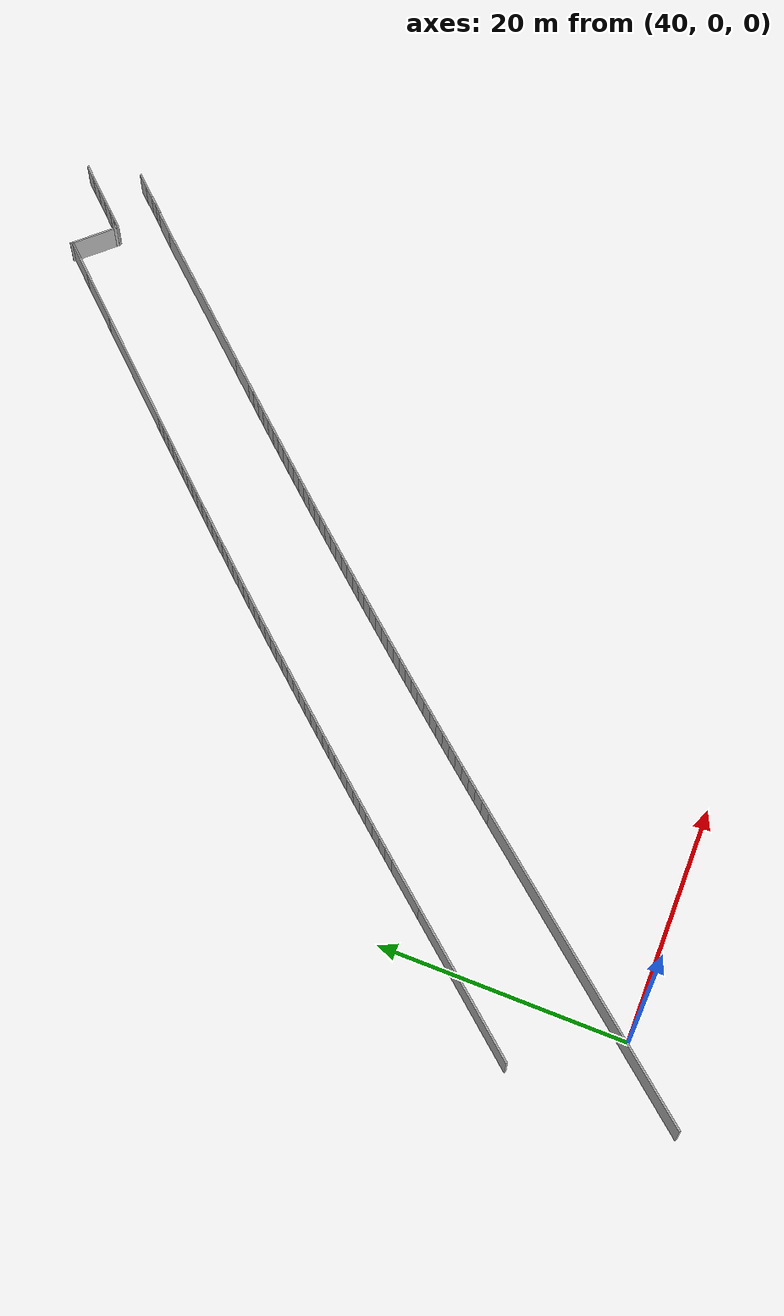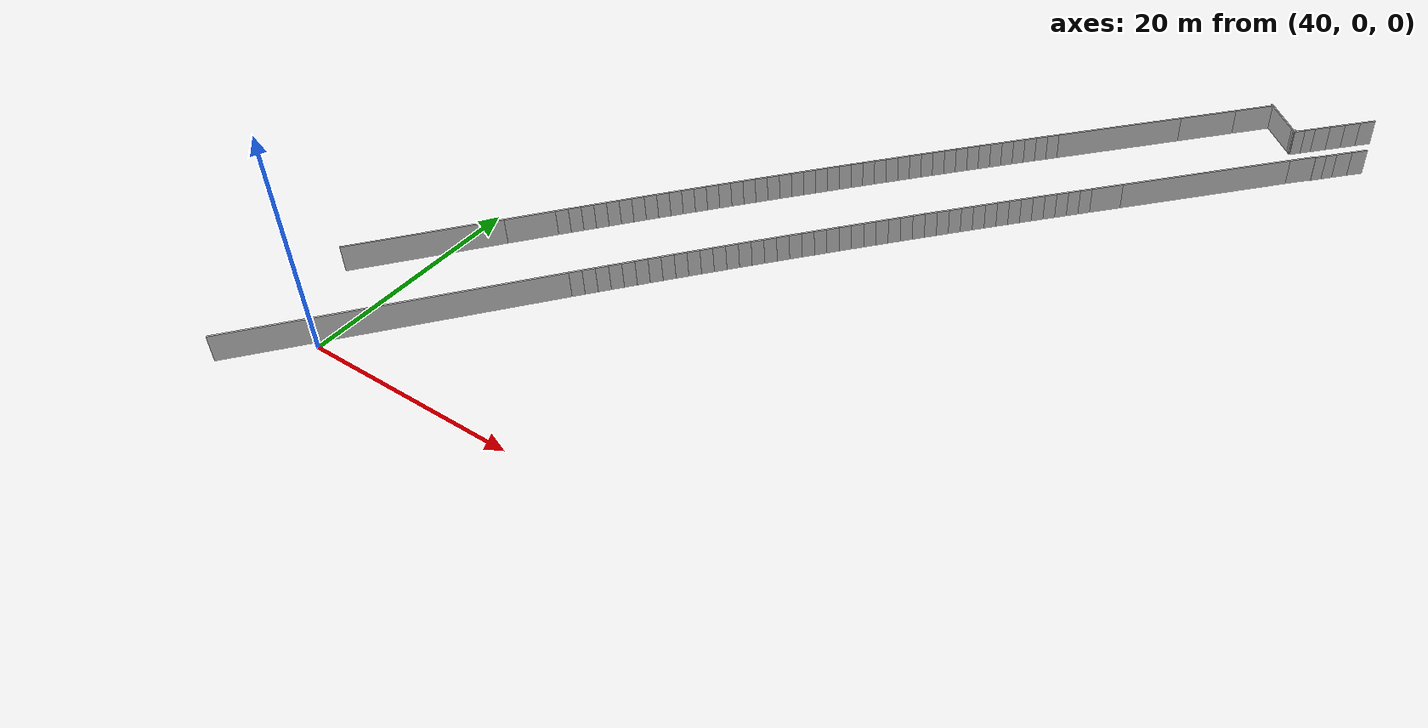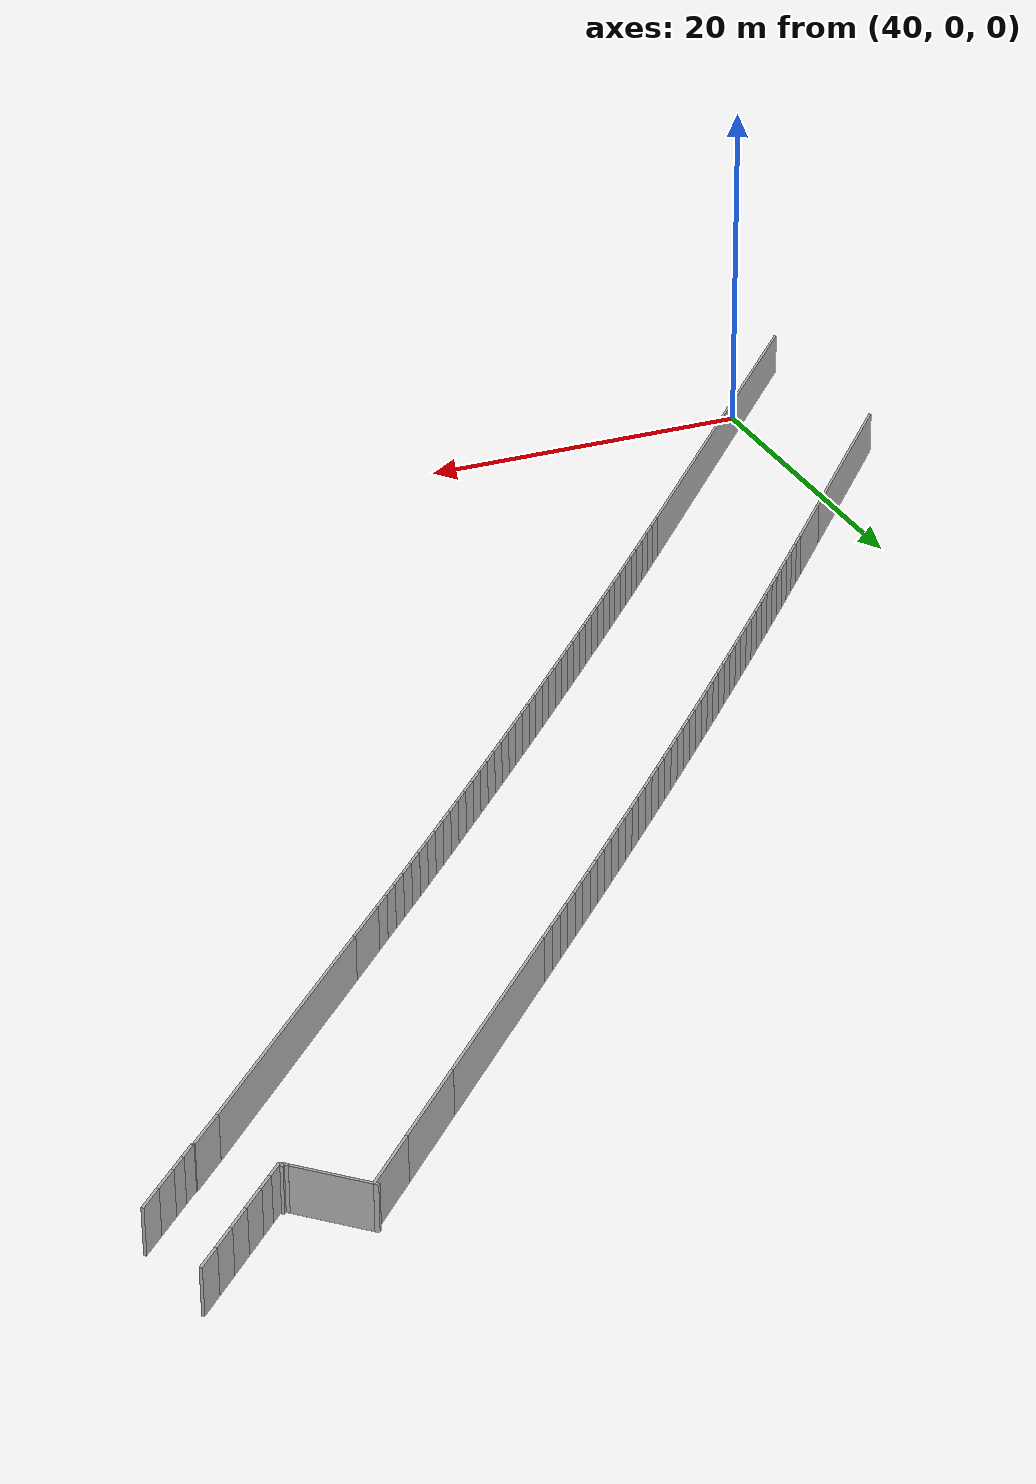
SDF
<?xml version="1.0" ?>
<sdf version="1.6">
  <model name="sps_0420">
    <pose frame="">0 0 0 0 -0 0</pose>
    <static>1</static>
    <self_collide>0</self_collide>
    <allow_auto_disable>0</allow_auto_disable>
    <link name="Wall45">
      <kinematic>0</kinematic>
      <gravity>1</gravity>
      <self_collide>0</self_collide>
      <collision name="collision">
        <geometry>
          <box>
            <size>0.246635 0.15 2.5</size>
          </box>
        </geometry>
        <pose frame="">0 0 0 0 -0 0</pose>
      </collision>
      <visual name="visual">
        <geometry>
          <box>
            <size>0.246635 0.15 2.5</size>
          </box>
        </geometry>
        <pose frame="">0 0 0 0 -0 0</pose>
        <cast_shadows>1</cast_shadows>
        <transparency>0.0</transparency>
      </visual>
      <pose frame="">90.7091 70.7286 1.25 0 0 -0.770349</pose>
    </link>
    <link name="Wall207">
      <kinematic>0</kinematic>
      <gravity>1</gravity>
      <self_collide>0</self_collide>
      <collision name="collision">
        <geometry>
          <box>
            <size>11.9252 0.15 2.5</size>
          </box>
        </geometry>
        <pose frame="">0 0 0 0 -0 0</pose>
      </collision>
      <visual name="visual">
        <geometry>
          <box>
            <size>11.9252 0.15 2.5</size>
          </box>
        </geometry>
        <pose frame="">0 0 0 0 -0 0</pose>
        <cast_shadows>1</cast_shadows>
        <transparency>0.0</transparency>
      </visual>
      <pose frame="">80.3936 59.5335 1.25 0 -0 0.818166</pose>
    </link>
    <link name="Wall208">
      <kinematic>0</kinematic>
      <gravity>1</gravity>
      <self_collide>0</self_collide>
      <collision name="collision">
        <geometry>
          <box>
            <size>5.4905 0.15 2.5</size>
          </box>
        </geometry>
        <pose frame="">0 0 0 0 -0 0</pose>
      </collision>
      <visual name="visual">
        <geometry>
          <box>
            <size>5.4905 0.15 2.5</size>
          </box>
        </geometry>
        <pose frame="">0 0 0 0 -0 0</pose>
        <cast_shadows>1</cast_shadows>
        <transparency>0.0</transparency>
      </visual>
      <pose frame="">86.346 65.8893 1.25 0 -0 0.818166</pose>
    </link>
    <link name="Wall209">
      <kinematic>0</kinematic>
      <gravity>1</gravity>
      <self_collide>0</self_collide>
      <collision name="collision">
        <geometry>
          <box>
            <size>3.76717 0.15 2.5</size>
          </box>
        </geometry>
        <pose frame="">0 0 0 0 -0 0</pose>
      </collision>
      <visual name="visual">
        <geometry>
          <box>
            <size>3.76717 0.15 2.5</size>
          </box>
        </geometry>
        <pose frame="">0 0 0 0 -0 0</pose>
        <cast_shadows>1</cast_shadows>
        <transparency>0.0</transparency>
      </visual>
      <pose frame="">89.5101 69.2679 1.25 0 -0 0.818166</pose>
    </link>
    <link name="Wall217">
      <kinematic>0</kinematic>
      <gravity>1</gravity>
      <self_collide>0</self_collide>
      <collision name="collision">
        <geometry>
          <box>
            <size>0.242788 0.15 2.5</size>
          </box>
        </geometry>
        <pose frame="">0 0 0 0 -0 0</pose>
      </collision>
      <visual name="visual">
        <geometry>
          <box>
            <size>0.242788 0.15 2.5</size>
          </box>
        </geometry>
        <pose frame="">0 0 0 0 -0 0</pose>
        <cast_shadows>1</cast_shadows>
        <transparency>0.0</transparency>
      </visual>
      <pose frame="">93.9666 67.7998 1.25 0 -0 0.876505</pose>
    </link>
    <link name="Wall369">
      <kinematic>0</kinematic>
      <gravity>1</gravity>
      <self_collide>0</self_collide>
      <collision name="collision">
        <geometry>
          <box>
            <size>0.175889 0.15 2.5</size>
          </box>
        </geometry>
        <pose frame="">0 0 0 0 -0 0</pose>
      </collision>
      <visual name="visual">
        <geometry>
          <box>
            <size>0.175889 0.15 2.5</size>
          </box>
        </geometry>
        <pose frame="">0 0 0 0 -0 0</pose>
        <cast_shadows>1</cast_shadows>
        <transparency>0.0</transparency>
      </visual>
      <pose frame="">93.9545 67.6479 1.25 0 0 -0.729178</pose>
    </link>
    <link name="Wall445">
      <kinematic>0</kinematic>
      <gravity>1</gravity>
      <self_collide>0</self_collide>
      <collision name="collision">
        <geometry>
          <box>
            <size>13.3956 0.15 2.5</size>
          </box>
        </geometry>
        <pose frame="">0 0 0 0 -0 0</pose>
      </collision>
      <visual name="visual">
        <geometry>
          <box>
            <size>13.3956 0.15 2.5</size>
          </box>
        </geometry>
        <pose frame="">0 0 0 0 -0 0</pose>
        <cast_shadows>1</cast_shadows>
        <transparency>0.0</transparency>
      </visual>
      <pose frame="">38.8002 12.7838 1.25 0 -0 0.867691</pose>
    </link>
    <link name="Wall446">
      <kinematic>0</kinematic>
      <gravity>1</gravity>
      <self_collide>0</self_collide>
      <collision name="collision">
        <geometry>
          <box>
            <size>4.31681 0.15 2.5</size>
          </box>
        </geometry>
        <pose frame="">0 0 0 0 -0 0</pose>
      </collision>
      <visual name="visual">
        <geometry>
          <box>
            <size>4.31681 0.15 2.5</size>
          </box>
        </geometry>
        <pose frame="">0 0 0 0 -0 0</pose>
        <cast_shadows>1</cast_shadows>
        <transparency>0.0</transparency>
      </visual>
      <pose frame="">44.5265 19.5396 1.25 0 -0 0.867691</pose>
    </link>
    <link name="Wall552">
      <kinematic>0</kinematic>
      <gravity>1</gravity>
      <self_collide>0</self_collide>
      <collision name="collision">
        <geometry>
          <box>
            <size>0.0508075 0.15 2.5</size>
          </box>
        </geometry>
        <pose frame="">0 0 0 0 -0 0</pose>
      </collision>
      <visual name="visual">
        <geometry>
          <box>
            <size>0.0508075 0.15 2.5</size>
          </box>
        </geometry>
        <pose frame="">0 0 0 0 -0 0</pose>
        <cast_shadows>1</cast_shadows>
        <transparency>0.0</transparency>
      </visual>
      <pose frame="">97.0051 64.7574 1.25 0 -0 2.25323</pose>
    </link>
    <link name="Wall620">
      <kinematic>0</kinematic>
      <gravity>1</gravity>
      <self_collide>0</self_collide>
      <collision name="collision">
        <geometry>
          <box>
            <size>27.7321 0.15 2.5</size>
          </box>
        </geometry>
        <pose frame="">0 0 0 0 -0 0</pose>
      </collision>
      <visual name="visual">
        <geometry>
          <box>
            <size>27.7321 0.15 2.5</size>
          </box>
        </geometry>
        <pose frame="">0 0 0 0 -0 0</pose>
        <cast_shadows>1</cast_shadows>
        <transparency>0.0</transparency>
      </visual>
      <pose frame="">43.4344 5.10415 1.25 0 -0 0.867753</pose>
    </link>
    <link name="Wall621">
      <kinematic>0</kinematic>
      <gravity>1</gravity>
      <self_collide>0</self_collide>
      <collision name="collision">
        <geometry>
          <box>
            <size>2.85277 0.15 2.5</size>
          </box>
        </geometry>
        <pose frame="">0 0 0 0 -0 0</pose>
      </collision>
      <visual name="visual">
        <geometry>
          <box>
            <size>2.85277 0.15 2.5</size>
          </box>
        </geometry>
        <pose frame="">0 0 0 0 -0 0</pose>
        <cast_shadows>1</cast_shadows>
        <transparency>0.0</transparency>
      </visual>
      <pose frame="">83.4944 50.4094 1.25 0 -0 0.818179</pose>
    </link>
    <link name="Wall622">
      <kinematic>0</kinematic>
      <gravity>1</gravity>
      <self_collide>0</self_collide>
      <collision name="collision">
        <geometry>
          <box>
            <size>15.8262 0.15 2.5</size>
          </box>
        </geometry>
        <pose frame="">0 0 0 0 -0 0</pose>
      </collision>
      <visual name="visual">
        <geometry>
          <box>
            <size>15.8262 0.15 2.5</size>
          </box>
        </geometry>
        <pose frame="">0 0 0 0 -0 0</pose>
        <cast_shadows>1</cast_shadows>
        <transparency>0.0</transparency>
      </visual>
      <pose frame="">89.8784 57.2263 1.25 0 -0 0.818179</pose>
    </link>
    <link name="Wall623">
      <kinematic>0</kinematic>
      <gravity>1</gravity>
      <self_collide>0</self_collide>
      <collision name="collision">
        <geometry>
          <box>
            <size>2.45889 0.15 2.5</size>
          </box>
        </geometry>
        <pose frame="">0 0 0 0 -0 0</pose>
      </collision>
      <visual name="visual">
        <geometry>
          <box>
            <size>2.45889 0.15 2.5</size>
          </box>
        </geometry>
        <pose frame="">0 0 0 0 -0 0</pose>
        <cast_shadows>1</cast_shadows>
        <transparency>0.0</transparency>
      </visual>
      <pose frame="">96.1382 63.8896 1.25 0 -0 0.806515</pose>
    </link>
    <link name="Wall671">
      <kinematic>0</kinematic>
      <gravity>1</gravity>
      <self_collide>0</self_collide>
      <collision name="collision">
        <geometry>
          <box>
            <size>0.270926 0.15 2.5</size>
          </box>
        </geometry>
        <pose frame="">0 0 0 0 -0 0</pose>
      </collision>
      <visual name="visual">
        <geometry>
          <box>
            <size>0.270926 0.15 2.5</size>
          </box>
        </geometry>
        <pose frame="">0 0 0 0 -0 0</pose>
        <cast_shadows>1</cast_shadows>
        <transparency>0.0</transparency>
      </visual>
      <pose frame="">93.7907 67.7998 1.25 0 -0 2.38191</pose>
    </link>
    <link name="Wall672">
      <kinematic>0</kinematic>
      <gravity>1</gravity>
      <self_collide>0</self_collide>
      <collision name="collision">
        <geometry>
          <box>
            <size>3.99255 0.15 2.5</size>
          </box>
        </geometry>
        <pose frame="">0 0 0 0 -0 0</pose>
      </collision>
      <visual name="visual">
        <geometry>
          <box>
            <size>3.99255 0.15 2.5</size>
          </box>
        </geometry>
        <pose frame="">0 0 0 0 -0 0</pose>
        <cast_shadows>1</cast_shadows>
        <transparency>0.0</transparency>
      </visual>
      <pose frame="">92.245 69.2679 1.25 0 -0 2.38191</pose>
    </link>
    <link name="Wall3413">
      <kinematic>0</kinematic>
      <gravity>1</gravity>
      <self_collide>0</self_collide>
      <collision name="collision">
        <geometry>
          <box>
            <size>1.49648 0.15 2.5</size>
          </box>
        </geometry>
        <pose frame="">0 0 0 0 -0 0</pose>
      </collision>
      <visual name="visual">
        <geometry>
          <box>
            <size>1.49648 0.15 2.5</size>
          </box>
        </geometry>
        <pose frame="">0 0 0 0 -0 0</pose>
        <cast_shadows>1</cast_shadows>
        <transparency>0.0</transparency>
      </visual>
      <pose frame="">99.9777 67.836 1.25 0 0 -2.33439</pose>
    </link>
    <link name="Wall3414">
      <kinematic>0</kinematic>
      <gravity>1</gravity>
      <self_collide>0</self_collide>
      <collision name="collision">
        <geometry>
          <box>
            <size>1.49651 0.15 2.5</size>
          </box>
        </geometry>
        <pose frame="">0 0 0 0 -0 0</pose>
      </collision>
      <visual name="visual">
        <geometry>
          <box>
            <size>1.49651 0.15 2.5</size>
          </box>
        </geometry>
        <pose frame="">0 0 0 0 -0 0</pose>
        <cast_shadows>1</cast_shadows>
        <transparency>0.0</transparency>
      </visual>
      <pose frame="">98.9438 66.754 1.25 0 0 -2.33246</pose>
    </link>
    <link name="Wall3415">
      <kinematic>0</kinematic>
      <gravity>1</gravity>
      <self_collide>0</self_collide>
      <collision name="collision">
        <geometry>
          <box>
            <size>1.01888 0.15 2.5</size>
          </box>
        </geometry>
        <pose frame="">0 0 0 0 -0 0</pose>
      </collision>
      <visual name="visual">
        <geometry>
          <box>
            <size>1.01888 0.15 2.5</size>
          </box>
        </geometry>
        <pose frame="">0 0 0 0 -0 0</pose>
        <cast_shadows>1</cast_shadows>
        <transparency>0.0</transparency>
      </visual>
      <pose frame="">98.0755 65.8442 1.25 0 0 -2.33357</pose>
    </link>
    <link name="Wall3416">
      <kinematic>0</kinematic>
      <gravity>1</gravity>
      <self_collide>0</self_collide>
      <collision name="collision">
        <geometry>
          <box>
            <size>1.01898 0.15 2.5</size>
          </box>
        </geometry>
        <pose frame="">0 0 0 0 -0 0</pose>
      </collision>
      <visual name="visual">
        <geometry>
          <box>
            <size>1.01898 0.15 2.5</size>
          </box>
        </geometry>
        <pose frame="">0 0 0 0 -0 0</pose>
        <cast_shadows>1</cast_shadows>
        <transparency>0.0</transparency>
      </visual>
      <pose frame="">97.3723 65.1068 1.25 0 0 -2.33133</pose>
    </link>
    <link name="Wall3577">
      <kinematic>0</kinematic>
      <gravity>1</gravity>
      <self_collide>0</self_collide>
      <collision name="collision">
        <geometry>
          <box>
            <size>1.08497 0.15 2.5</size>
          </box>
        </geometry>
        <pose frame="">0 0 0 0 -0 0</pose>
      </collision>
      <visual name="visual">
        <geometry>
          <box>
            <size>1.08497 0.15 2.5</size>
          </box>
        </geometry>
        <pose frame="">0 0 0 0 -0 0</pose>
        <cast_shadows>1</cast_shadows>
        <transparency>0.0</transparency>
      </visual>
      <pose frame="">75.947 54.7856 1.25 0 0 -2.32357</pose>
    </link>
    <link name="Wall3578">
      <kinematic>0</kinematic>
      <gravity>1</gravity>
      <self_collide>0</self_collide>
      <collision name="collision">
        <geometry>
          <box>
            <size>1.08475 0.15 2.5</size>
          </box>
        </geometry>
        <pose frame="">0 0 0 0 -0 0</pose>
      </collision>
      <visual name="visual">
        <geometry>
          <box>
            <size>1.08475 0.15 2.5</size>
          </box>
        </geometry>
        <pose frame="">0 0 0 0 -0 0</pose>
        <cast_shadows>1</cast_shadows>
        <transparency>0.0</transparency>
      </visual>
      <pose frame="">75.2056 53.9935 1.25 0 0 -2.32261</pose>
    </link>
    <link name="Wall3579">
      <kinematic>0</kinematic>
      <gravity>1</gravity>
      <self_collide>0</self_collide>
      <collision name="collision">
        <geometry>
          <box>
            <size>1.08479 0.15 2.5</size>
          </box>
        </geometry>
        <pose frame="">0 0 0 0 -0 0</pose>
      </collision>
      <visual name="visual">
        <geometry>
          <box>
            <size>1.08479 0.15 2.5</size>
          </box>
        </geometry>
        <pose frame="">0 0 0 0 -0 0</pose>
        <cast_shadows>1</cast_shadows>
        <transparency>0.0</transparency>
      </visual>
      <pose frame="">74.4652 53.2007 1.25 0 0 -2.3215</pose>
    </link>
    <link name="Wall3580">
      <kinematic>0</kinematic>
      <gravity>1</gravity>
      <self_collide>0</self_collide>
      <collision name="collision">
        <geometry>
          <box>
            <size>1.08566 0.15 2.5</size>
          </box>
        </geometry>
        <pose frame="">0 0 0 0 -0 0</pose>
      </collision>
      <visual name="visual">
        <geometry>
          <box>
            <size>1.08566 0.15 2.5</size>
          </box>
        </geometry>
        <pose frame="">0 0 0 0 -0 0</pose>
        <cast_shadows>1</cast_shadows>
        <transparency>0.0</transparency>
      </visual>
      <pose frame="">73.7255 52.4067 1.25 0 0 -2.32021</pose>
    </link>
    <link name="Wall3581">
      <kinematic>0</kinematic>
      <gravity>1</gravity>
      <self_collide>0</self_collide>
      <collision name="collision">
        <geometry>
          <box>
            <size>1.08574 0.15 2.5</size>
          </box>
        </geometry>
        <pose frame="">0 0 0 0 -0 0</pose>
      </collision>
      <visual name="visual">
        <geometry>
          <box>
            <size>1.08574 0.15 2.5</size>
          </box>
        </geometry>
        <pose frame="">0 0 0 0 -0 0</pose>
        <cast_shadows>1</cast_shadows>
        <transparency>0.0</transparency>
      </visual>
      <pose frame="">72.9863 51.6115 1.25 0 0 -2.31922</pose>
    </link>
    <link name="Wall3582">
      <kinematic>0</kinematic>
      <gravity>1</gravity>
      <self_collide>0</self_collide>
      <collision name="collision">
        <geometry>
          <box>
            <size>1.08574 0.15 2.5</size>
          </box>
        </geometry>
        <pose frame="">0 0 0 0 -0 0</pose>
      </collision>
      <visual name="visual">
        <geometry>
          <box>
            <size>1.08574 0.15 2.5</size>
          </box>
        </geometry>
        <pose frame="">0 0 0 0 -0 0</pose>
        <cast_shadows>1</cast_shadows>
        <transparency>0.0</transparency>
      </visual>
      <pose frame="">72.2479 50.8155 1.25 0 0 -2.31814</pose>
    </link>
    <link name="Wall3583">
      <kinematic>0</kinematic>
      <gravity>1</gravity>
      <self_collide>0</self_collide>
      <collision name="collision">
        <geometry>
          <box>
            <size>1.08572 0.15 2.5</size>
          </box>
        </geometry>
        <pose frame="">0 0 0 0 -0 0</pose>
      </collision>
      <visual name="visual">
        <geometry>
          <box>
            <size>1.08572 0.15 2.5</size>
          </box>
        </geometry>
        <pose frame="">0 0 0 0 -0 0</pose>
        <cast_shadows>1</cast_shadows>
        <transparency>0.0</transparency>
      </visual>
      <pose frame="">71.5105 50.0186 1.25 0 0 -2.31671</pose>
    </link>
    <link name="Wall3584">
      <kinematic>0</kinematic>
      <gravity>1</gravity>
      <self_collide>0</self_collide>
      <collision name="collision">
        <geometry>
          <box>
            <size>1.08576 0.15 2.5</size>
          </box>
        </geometry>
        <pose frame="">0 0 0 0 -0 0</pose>
      </collision>
      <visual name="visual">
        <geometry>
          <box>
            <size>1.08576 0.15 2.5</size>
          </box>
        </geometry>
        <pose frame="">0 0 0 0 -0 0</pose>
        <cast_shadows>1</cast_shadows>
        <transparency>0.0</transparency>
      </visual>
      <pose frame="">70.774 49.2208 1.25 0 0 -2.31568</pose>
    </link>
    <link name="Wall3585">
      <kinematic>0</kinematic>
      <gravity>1</gravity>
      <self_collide>0</self_collide>
      <collision name="collision">
        <geometry>
          <box>
            <size>1.08559 0.15 2.5</size>
          </box>
        </geometry>
        <pose frame="">0 0 0 0 -0 0</pose>
      </collision>
      <visual name="visual">
        <geometry>
          <box>
            <size>1.08559 0.15 2.5</size>
          </box>
        </geometry>
        <pose frame="">0 0 0 0 -0 0</pose>
        <cast_shadows>1</cast_shadows>
        <transparency>0.0</transparency>
      </visual>
      <pose frame="">70.0384 48.4223 1.25 0 0 -2.31476</pose>
    </link>
    <link name="Wall3586">
      <kinematic>0</kinematic>
      <gravity>1</gravity>
      <self_collide>0</self_collide>
      <collision name="collision">
        <geometry>
          <box>
            <size>1.08569 0.15 2.5</size>
          </box>
        </geometry>
        <pose frame="">0 0 0 0 -0 0</pose>
      </collision>
      <visual name="visual">
        <geometry>
          <box>
            <size>1.08569 0.15 2.5</size>
          </box>
        </geometry>
        <pose frame="">0 0 0 0 -0 0</pose>
        <cast_shadows>1</cast_shadows>
        <transparency>0.0</transparency>
      </visual>
      <pose frame="">69.3038 47.623 1.25 0 0 -2.31345</pose>
    </link>
    <link name="Wall3587">
      <kinematic>0</kinematic>
      <gravity>1</gravity>
      <self_collide>0</self_collide>
      <collision name="collision">
        <geometry>
          <box>
            <size>1.08587 0.15 2.5</size>
          </box>
        </geometry>
        <pose frame="">0 0 0 0 -0 0</pose>
      </collision>
      <visual name="visual">
        <geometry>
          <box>
            <size>1.08587 0.15 2.5</size>
          </box>
        </geometry>
        <pose frame="">0 0 0 0 -0 0</pose>
        <cast_shadows>1</cast_shadows>
        <transparency>0.0</transparency>
      </visual>
      <pose frame="">68.57 46.8227 1.25 0 0 -2.3123</pose>
    </link>
    <link name="Wall3588">
      <kinematic>0</kinematic>
      <gravity>1</gravity>
      <self_collide>0</self_collide>
      <collision name="collision">
        <geometry>
          <box>
            <size>1.08571 0.15 2.5</size>
          </box>
        </geometry>
        <pose frame="">0 0 0 0 -0 0</pose>
      </collision>
      <visual name="visual">
        <geometry>
          <box>
            <size>1.08571 0.15 2.5</size>
          </box>
        </geometry>
        <pose frame="">0 0 0 0 -0 0</pose>
        <cast_shadows>1</cast_shadows>
        <transparency>0.0</transparency>
      </visual>
      <pose frame="">67.8371 46.0216 1.25 0 0 -2.31122</pose>
    </link>
    <link name="Wall3589">
      <kinematic>0</kinematic>
      <gravity>1</gravity>
      <self_collide>0</self_collide>
      <collision name="collision">
        <geometry>
          <box>
            <size>1.08581 0.15 2.5</size>
          </box>
        </geometry>
        <pose frame="">0 0 0 0 -0 0</pose>
      </collision>
      <visual name="visual">
        <geometry>
          <box>
            <size>1.08581 0.15 2.5</size>
          </box>
        </geometry>
        <pose frame="">0 0 0 0 -0 0</pose>
        <cast_shadows>1</cast_shadows>
        <transparency>0.0</transparency>
      </visual>
      <pose frame="">67.1051 45.2197 1.25 0 0 -2.31007</pose>
    </link>
    <link name="Wall3590">
      <kinematic>0</kinematic>
      <gravity>1</gravity>
      <self_collide>0</self_collide>
      <collision name="collision">
        <geometry>
          <box>
            <size>1.08583 0.15 2.5</size>
          </box>
        </geometry>
        <pose frame="">0 0 0 0 -0 0</pose>
      </collision>
      <visual name="visual">
        <geometry>
          <box>
            <size>1.08583 0.15 2.5</size>
          </box>
        </geometry>
        <pose frame="">0 0 0 0 -0 0</pose>
        <cast_shadows>1</cast_shadows>
        <transparency>0.0</transparency>
      </visual>
      <pose frame="">66.374 44.4169 1.25 0 0 -2.30892</pose>
    </link>
    <link name="Wall3591">
      <kinematic>0</kinematic>
      <gravity>1</gravity>
      <self_collide>0</self_collide>
      <collision name="collision">
        <geometry>
          <box>
            <size>1.08563 0.15 2.5</size>
          </box>
        </geometry>
        <pose frame="">0 0 0 0 -0 0</pose>
      </collision>
      <visual name="visual">
        <geometry>
          <box>
            <size>1.08563 0.15 2.5</size>
          </box>
        </geometry>
        <pose frame="">0 0 0 0 -0 0</pose>
        <cast_shadows>1</cast_shadows>
        <transparency>0.0</transparency>
      </visual>
      <pose frame="">65.6439 43.6133 1.25 0 0 -2.30772</pose>
    </link>
    <link name="Wall3592">
      <kinematic>0</kinematic>
      <gravity>1</gravity>
      <self_collide>0</self_collide>
      <collision name="collision">
        <geometry>
          <box>
            <size>1.08565 0.15 2.5</size>
          </box>
        </geometry>
        <pose frame="">0 0 0 0 -0 0</pose>
      </collision>
      <visual name="visual">
        <geometry>
          <box>
            <size>1.08565 0.15 2.5</size>
          </box>
        </geometry>
        <pose frame="">0 0 0 0 -0 0</pose>
        <cast_shadows>1</cast_shadows>
        <transparency>0.0</transparency>
      </visual>
      <pose frame="">64.9148 42.8089 1.25 0 0 -2.30656</pose>
    </link>
    <link name="Wall3593">
      <kinematic>0</kinematic>
      <gravity>1</gravity>
      <self_collide>0</self_collide>
      <collision name="collision">
        <geometry>
          <box>
            <size>1.08566 0.15 2.5</size>
          </box>
        </geometry>
        <pose frame="">0 0 0 0 -0 0</pose>
      </collision>
      <visual name="visual">
        <geometry>
          <box>
            <size>1.08566 0.15 2.5</size>
          </box>
        </geometry>
        <pose frame="">0 0 0 0 -0 0</pose>
        <cast_shadows>1</cast_shadows>
        <transparency>0.0</transparency>
      </visual>
      <pose frame="">64.1865 42.0037 1.25 0 0 -2.30549</pose>
    </link>
    <link name="Wall3594">
      <kinematic>0</kinematic>
      <gravity>1</gravity>
      <self_collide>0</self_collide>
      <collision name="collision">
        <geometry>
          <box>
            <size>1.08604 0.15 2.5</size>
          </box>
        </geometry>
        <pose frame="">0 0 0 0 -0 0</pose>
      </collision>
      <visual name="visual">
        <geometry>
          <box>
            <size>1.08604 0.15 2.5</size>
          </box>
        </geometry>
        <pose frame="">0 0 0 0 -0 0</pose>
        <cast_shadows>1</cast_shadows>
        <transparency>0.0</transparency>
      </visual>
      <pose frame="">63.4592 41.1975 1.25 0 0 -2.30419</pose>
    </link>
    <link name="Wall3595">
      <kinematic>0</kinematic>
      <gravity>1</gravity>
      <self_collide>0</self_collide>
      <collision name="collision">
        <geometry>
          <box>
            <size>1.08579 0.15 2.5</size>
          </box>
        </geometry>
        <pose frame="">0 0 0 0 -0 0</pose>
      </collision>
      <visual name="visual">
        <geometry>
          <box>
            <size>1.08579 0.15 2.5</size>
          </box>
        </geometry>
        <pose frame="">0 0 0 0 -0 0</pose>
        <cast_shadows>1</cast_shadows>
        <transparency>0.0</transparency>
      </visual>
      <pose frame="">62.7327 40.3904 1.25 0 0 -2.30319</pose>
    </link>
    <link name="Wall3596">
      <kinematic>0</kinematic>
      <gravity>1</gravity>
      <self_collide>0</self_collide>
      <collision name="collision">
        <geometry>
          <box>
            <size>1.08574 0.15 2.5</size>
          </box>
        </geometry>
        <pose frame="">0 0 0 0 -0 0</pose>
      </collision>
      <visual name="visual">
        <geometry>
          <box>
            <size>1.08574 0.15 2.5</size>
          </box>
        </geometry>
        <pose frame="">0 0 0 0 -0 0</pose>
        <cast_shadows>1</cast_shadows>
        <transparency>0.0</transparency>
      </visual>
      <pose frame="">62.0072 39.5826 1.25 0 0 -2.30195</pose>
    </link>
    <link name="Wall3597">
      <kinematic>0</kinematic>
      <gravity>1</gravity>
      <self_collide>0</self_collide>
      <collision name="collision">
        <geometry>
          <box>
            <size>1.08579 0.15 2.5</size>
          </box>
        </geometry>
        <pose frame="">0 0 0 0 -0 0</pose>
      </collision>
      <visual name="visual">
        <geometry>
          <box>
            <size>1.08579 0.15 2.5</size>
          </box>
        </geometry>
        <pose frame="">0 0 0 0 -0 0</pose>
        <cast_shadows>1</cast_shadows>
        <transparency>0.0</transparency>
      </visual>
      <pose frame="">61.2826 38.774 1.25 0 0 -2.301</pose>
    </link>
    <link name="Wall3598">
      <kinematic>0</kinematic>
      <gravity>1</gravity>
      <self_collide>0</self_collide>
      <collision name="collision">
        <geometry>
          <box>
            <size>1.0856 0.15 2.5</size>
          </box>
        </geometry>
        <pose frame="">0 0 0 0 -0 0</pose>
      </collision>
      <visual name="visual">
        <geometry>
          <box>
            <size>1.0856 0.15 2.5</size>
          </box>
        </geometry>
        <pose frame="">0 0 0 0 -0 0</pose>
        <cast_shadows>1</cast_shadows>
        <transparency>0.0</transparency>
      </visual>
      <pose frame="">60.5588 37.9647 1.25 0 0 -2.29987</pose>
    </link>
    <link name="Wall3599">
      <kinematic>0</kinematic>
      <gravity>1</gravity>
      <self_collide>0</self_collide>
      <collision name="collision">
        <geometry>
          <box>
            <size>1.08576 0.15 2.5</size>
          </box>
        </geometry>
        <pose frame="">0 0 0 0 -0 0</pose>
      </collision>
      <visual name="visual">
        <geometry>
          <box>
            <size>1.08576 0.15 2.5</size>
          </box>
        </geometry>
        <pose frame="">0 0 0 0 -0 0</pose>
        <cast_shadows>1</cast_shadows>
        <transparency>0.0</transparency>
      </visual>
      <pose frame="">59.8361 37.1546 1.25 0 0 -2.29869</pose>
    </link>
    <link name="Wall3600">
      <kinematic>0</kinematic>
      <gravity>1</gravity>
      <self_collide>0</self_collide>
      <collision name="collision">
        <geometry>
          <box>
            <size>1.08574 0.15 2.5</size>
          </box>
        </geometry>
        <pose frame="">0 0 0 0 -0 0</pose>
      </collision>
      <visual name="visual">
        <geometry>
          <box>
            <size>1.08574 0.15 2.5</size>
          </box>
        </geometry>
        <pose frame="">0 0 0 0 -0 0</pose>
        <cast_shadows>1</cast_shadows>
        <transparency>0.0</transparency>
      </visual>
      <pose frame="">59.1142 36.3436 1.25 0 0 -2.29757</pose>
    </link>
    <link name="Wall3601">
      <kinematic>0</kinematic>
      <gravity>1</gravity>
      <self_collide>0</self_collide>
      <collision name="collision">
        <geometry>
          <box>
            <size>1.08565 0.15 2.5</size>
          </box>
        </geometry>
        <pose frame="">0 0 0 0 -0 0</pose>
      </collision>
      <visual name="visual">
        <geometry>
          <box>
            <size>1.08565 0.15 2.5</size>
          </box>
        </geometry>
        <pose frame="">0 0 0 0 -0 0</pose>
        <cast_shadows>1</cast_shadows>
        <transparency>0.0</transparency>
      </visual>
      <pose frame="">58.3932 35.5318 1.25 0 0 -2.29637</pose>
    </link>
    <link name="Wall3602">
      <kinematic>0</kinematic>
      <gravity>1</gravity>
      <self_collide>0</self_collide>
      <collision name="collision">
        <geometry>
          <box>
            <size>1.08572 0.15 2.5</size>
          </box>
        </geometry>
        <pose frame="">0 0 0 0 -0 0</pose>
      </collision>
      <visual name="visual">
        <geometry>
          <box>
            <size>1.08572 0.15 2.5</size>
          </box>
        </geometry>
        <pose frame="">0 0 0 0 -0 0</pose>
        <cast_shadows>1</cast_shadows>
        <transparency>0.0</transparency>
      </visual>
      <pose frame="">57.6732 34.7192 1.25 0 0 -2.29534</pose>
    </link>
    <link name="Wall3603">
      <kinematic>0</kinematic>
      <gravity>1</gravity>
      <self_collide>0</self_collide>
      <collision name="collision">
        <geometry>
          <box>
            <size>1.08569 0.15 2.5</size>
          </box>
        </geometry>
        <pose frame="">0 0 0 0 -0 0</pose>
      </collision>
      <visual name="visual">
        <geometry>
          <box>
            <size>1.08569 0.15 2.5</size>
          </box>
        </geometry>
        <pose frame="">0 0 0 0 -0 0</pose>
        <cast_shadows>1</cast_shadows>
        <transparency>0.0</transparency>
      </visual>
      <pose frame="">56.9542 33.9057 1.25 0 0 -2.29386</pose>
    </link>
    <link name="Wall3604">
      <kinematic>0</kinematic>
      <gravity>1</gravity>
      <self_collide>0</self_collide>
      <collision name="collision">
        <geometry>
          <box>
            <size>1.08569 0.15 2.5</size>
          </box>
        </geometry>
        <pose frame="">0 0 0 0 -0 0</pose>
      </collision>
      <visual name="visual">
        <geometry>
          <box>
            <size>1.08569 0.15 2.5</size>
          </box>
        </geometry>
        <pose frame="">0 0 0 0 -0 0</pose>
        <cast_shadows>1</cast_shadows>
        <transparency>0.0</transparency>
      </visual>
      <pose frame="">56.2362 33.0914 1.25 0 0 -2.29311</pose>
    </link>
    <link name="Wall3605">
      <kinematic>0</kinematic>
      <gravity>1</gravity>
      <self_collide>0</self_collide>
      <collision name="collision">
        <geometry>
          <box>
            <size>1.08583 0.15 2.5</size>
          </box>
        </geometry>
        <pose frame="">0 0 0 0 -0 0</pose>
      </collision>
      <visual name="visual">
        <geometry>
          <box>
            <size>1.08583 0.15 2.5</size>
          </box>
        </geometry>
        <pose frame="">0 0 0 0 -0 0</pose>
        <cast_shadows>1</cast_shadows>
        <transparency>0.0</transparency>
      </visual>
      <pose frame="">55.5189 32.2763 1.25 0 0 -2.2918</pose>
    </link>
    <link name="Wall3606">
      <kinematic>0</kinematic>
      <gravity>1</gravity>
      <self_collide>0</self_collide>
      <collision name="collision">
        <geometry>
          <box>
            <size>1.08578 0.15 2.5</size>
          </box>
        </geometry>
        <pose frame="">0 0 0 0 -0 0</pose>
      </collision>
      <visual name="visual">
        <geometry>
          <box>
            <size>1.08578 0.15 2.5</size>
          </box>
        </geometry>
        <pose frame="">0 0 0 0 -0 0</pose>
        <cast_shadows>1</cast_shadows>
        <transparency>0.0</transparency>
      </visual>
      <pose frame="">54.8026 31.4603 1.25 0 0 -2.29064</pose>
    </link>
    <link name="Wall3607">
      <kinematic>0</kinematic>
      <gravity>1</gravity>
      <self_collide>0</self_collide>
      <collision name="collision">
        <geometry>
          <box>
            <size>1.08569 0.15 2.5</size>
          </box>
        </geometry>
        <pose frame="">0 0 0 0 -0 0</pose>
      </collision>
      <visual name="visual">
        <geometry>
          <box>
            <size>1.08569 0.15 2.5</size>
          </box>
        </geometry>
        <pose frame="">0 0 0 0 -0 0</pose>
        <cast_shadows>1</cast_shadows>
        <transparency>0.0</transparency>
      </visual>
      <pose frame="">54.0873 30.6435 1.25 0 0 -2.28944</pose>
    </link>
    <link name="Wall3608">
      <kinematic>0</kinematic>
      <gravity>1</gravity>
      <self_collide>0</self_collide>
      <collision name="collision">
        <geometry>
          <box>
            <size>1.08581 0.15 2.5</size>
          </box>
        </geometry>
        <pose frame="">0 0 0 0 -0 0</pose>
      </collision>
      <visual name="visual">
        <geometry>
          <box>
            <size>1.08581 0.15 2.5</size>
          </box>
        </geometry>
        <pose frame="">0 0 0 0 -0 0</pose>
        <cast_shadows>1</cast_shadows>
        <transparency>0.0</transparency>
      </visual>
      <pose frame="">53.3729 29.8259 1.25 0 0 -2.28845</pose>
    </link>
    <link name="Wall3609">
      <kinematic>0</kinematic>
      <gravity>1</gravity>
      <self_collide>0</self_collide>
      <collision name="collision">
        <geometry>
          <box>
            <size>1.08568 0.15 2.5</size>
          </box>
        </geometry>
        <pose frame="">0 0 0 0 -0 0</pose>
      </collision>
      <visual name="visual">
        <geometry>
          <box>
            <size>1.08568 0.15 2.5</size>
          </box>
        </geometry>
        <pose frame="">0 0 0 0 -0 0</pose>
        <cast_shadows>1</cast_shadows>
        <transparency>0.0</transparency>
      </visual>
      <pose frame="">52.6594 29.0075 1.25 0 0 -2.28721</pose>
    </link>
    <link name="Wall3610">
      <kinematic>0</kinematic>
      <gravity>1</gravity>
      <self_collide>0</self_collide>
      <collision name="collision">
        <geometry>
          <box>
            <size>1.08568 0.15 2.5</size>
          </box>
        </geometry>
        <pose frame="">0 0 0 0 -0 0</pose>
      </collision>
      <visual name="visual">
        <geometry>
          <box>
            <size>1.08568 0.15 2.5</size>
          </box>
        </geometry>
        <pose frame="">0 0 0 0 -0 0</pose>
        <cast_shadows>1</cast_shadows>
        <transparency>0.0</transparency>
      </visual>
      <pose frame="">51.9469 28.1883 1.25 0 0 -2.28609</pose>
    </link>
    <link name="Wall3611">
      <kinematic>0</kinematic>
      <gravity>1</gravity>
      <self_collide>0</self_collide>
      <collision name="collision">
        <geometry>
          <box>
            <size>1.08563 0.15 2.5</size>
          </box>
        </geometry>
        <pose frame="">0 0 0 0 -0 0</pose>
      </collision>
      <visual name="visual">
        <geometry>
          <box>
            <size>1.08563 0.15 2.5</size>
          </box>
        </geometry>
        <pose frame="">0 0 0 0 -0 0</pose>
        <cast_shadows>1</cast_shadows>
        <transparency>0.0</transparency>
      </visual>
      <pose frame="">51.2353 27.3684 1.25 0 0 -2.28509</pose>
    </link>
    <link name="Wall3612">
      <kinematic>0</kinematic>
      <gravity>1</gravity>
      <self_collide>0</self_collide>
      <collision name="collision">
        <geometry>
          <box>
            <size>1.08568 0.15 2.5</size>
          </box>
        </geometry>
        <pose frame="">0 0 0 0 -0 0</pose>
      </collision>
      <visual name="visual">
        <geometry>
          <box>
            <size>1.08568 0.15 2.5</size>
          </box>
        </geometry>
        <pose frame="">0 0 0 0 -0 0</pose>
        <cast_shadows>1</cast_shadows>
        <transparency>0.0</transparency>
      </visual>
      <pose frame="">50.5246 26.5477 1.25 0 0 -2.28386</pose>
    </link>
    <link name="Wall3613">
      <kinematic>0</kinematic>
      <gravity>1</gravity>
      <self_collide>0</self_collide>
      <collision name="collision">
        <geometry>
          <box>
            <size>1.08581 0.15 2.5</size>
          </box>
        </geometry>
        <pose frame="">0 0 0 0 -0 0</pose>
      </collision>
      <visual name="visual">
        <geometry>
          <box>
            <size>1.08581 0.15 2.5</size>
          </box>
        </geometry>
        <pose frame="">0 0 0 0 -0 0</pose>
        <cast_shadows>1</cast_shadows>
        <transparency>0.0</transparency>
      </visual>
      <pose frame="">49.8148 25.7261 1.25 0 0 -2.28279</pose>
    </link>
    <link name="Wall3614">
      <kinematic>0</kinematic>
      <gravity>1</gravity>
      <self_collide>0</self_collide>
      <collision name="collision">
        <geometry>
          <box>
            <size>1.08575 0.15 2.5</size>
          </box>
        </geometry>
        <pose frame="">0 0 0 0 -0 0</pose>
      </collision>
      <visual name="visual">
        <geometry>
          <box>
            <size>1.08575 0.15 2.5</size>
          </box>
        </geometry>
        <pose frame="">0 0 0 0 -0 0</pose>
        <cast_shadows>1</cast_shadows>
        <transparency>0.0</transparency>
      </visual>
      <pose frame="">49.1059 24.9036 1.25 0 0 -2.28136</pose>
    </link>
    <link name="Wall3615">
      <kinematic>0</kinematic>
      <gravity>1</gravity>
      <self_collide>0</self_collide>
      <collision name="collision">
        <geometry>
          <box>
            <size>1.08582 0.15 2.5</size>
          </box>
        </geometry>
        <pose frame="">0 0 0 0 -0 0</pose>
      </collision>
      <visual name="visual">
        <geometry>
          <box>
            <size>1.08582 0.15 2.5</size>
          </box>
        </geometry>
        <pose frame="">0 0 0 0 -0 0</pose>
        <cast_shadows>1</cast_shadows>
        <transparency>0.0</transparency>
      </visual>
      <pose frame="">48.3981 24.0803 1.25 0 0 -2.28056</pose>
    </link>
    <link name="Wall3616">
      <kinematic>0</kinematic>
      <gravity>1</gravity>
      <self_collide>0</self_collide>
      <collision name="collision">
        <geometry>
          <box>
            <size>1.08849 0.15 2.5</size>
          </box>
        </geometry>
        <pose frame="">0 0 0 0 -0 0</pose>
      </collision>
      <visual name="visual">
        <geometry>
          <box>
            <size>1.08849 0.15 2.5</size>
          </box>
        </geometry>
        <pose frame="">0 0 0 0 -0 0</pose>
        <cast_shadows>1</cast_shadows>
        <transparency>0.0</transparency>
      </visual>
      <pose frame="">47.6902 23.2552 1.25 0 0 -2.2792</pose>
    </link>
    <link name="Wall3617">
      <kinematic>0</kinematic>
      <gravity>1</gravity>
      <self_collide>0</self_collide>
      <collision name="collision">
        <geometry>
          <box>
            <size>1.08857 0.15 2.5</size>
          </box>
        </geometry>
        <pose frame="">0 0 0 0 -0 0</pose>
      </collision>
      <visual name="visual">
        <geometry>
          <box>
            <size>1.08857 0.15 2.5</size>
          </box>
        </geometry>
        <pose frame="">0 0 0 0 -0 0</pose>
        <cast_shadows>1</cast_shadows>
        <transparency>0.0</transparency>
      </visual>
      <pose frame="">46.9824 22.4282 1.25 0 0 -2.27817</pose>
    </link>
    <link name="Wall3618">
      <kinematic>0</kinematic>
      <gravity>1</gravity>
      <self_collide>0</self_collide>
      <collision name="collision">
        <geometry>
          <box>
            <size>1.0888 0.15 2.5</size>
          </box>
        </geometry>
        <pose frame="">0 0 0 0 -0 0</pose>
      </collision>
      <visual name="visual">
        <geometry>
          <box>
            <size>1.0888 0.15 2.5</size>
          </box>
        </geometry>
        <pose frame="">0 0 0 0 -0 0</pose>
        <cast_shadows>1</cast_shadows>
        <transparency>0.0</transparency>
      </visual>
      <pose frame="">46.2754 21.6003 1.25 0 0 -2.27703</pose>
    </link>
    <link name="Wall6022">
      <kinematic>0</kinematic>
      <gravity>1</gravity>
      <self_collide>0</self_collide>
      <collision name="collision">
        <geometry>
          <box>
            <size>1.503 0.15 2.5</size>
          </box>
        </geometry>
        <pose frame="">0 0 0 0 -0 0</pose>
      </collision>
      <visual name="visual">
        <geometry>
          <box>
            <size>1.503 0.15 2.5</size>
          </box>
        </geometry>
        <pose frame="">0 0 0 0 -0 0</pose>
        <cast_shadows>1</cast_shadows>
        <transparency>0.0</transparency>
      </visual>
      <pose frame="">99.0581 72.856 1.25 0 0 -2.33739</pose>
    </link>
    <link name="Wall6023">
      <kinematic>0</kinematic>
      <gravity>1</gravity>
      <self_collide>0</self_collide>
      <collision name="collision">
        <geometry>
          <box>
            <size>1.50304 0.15 2.5</size>
          </box>
        </geometry>
        <pose frame="">0 0 0 0 -0 0</pose>
      </collision>
      <visual name="visual">
        <geometry>
          <box>
            <size>1.50304 0.15 2.5</size>
          </box>
        </geometry>
        <pose frame="">0 0 0 0 -0 0</pose>
        <cast_shadows>1</cast_shadows>
        <transparency>0.0</transparency>
      </visual>
      <pose frame="">98.0163 71.7726 1.25 0 0 -2.33583</pose>
    </link>
    <link name="Wall6024">
      <kinematic>0</kinematic>
      <gravity>1</gravity>
      <self_collide>0</self_collide>
      <collision name="collision">
        <geometry>
          <box>
            <size>1.50314 0.15 2.5</size>
          </box>
        </geometry>
        <pose frame="">0 0 0 0 -0 0</pose>
      </collision>
      <visual name="visual">
        <geometry>
          <box>
            <size>1.50314 0.15 2.5</size>
          </box>
        </geometry>
        <pose frame="">0 0 0 0 -0 0</pose>
        <cast_shadows>1</cast_shadows>
        <transparency>0.0</transparency>
      </visual>
      <pose frame="">96.9762 70.6875 1.25 0 0 -2.3342</pose>
    </link>
    <link name="Wall6025">
      <kinematic>0</kinematic>
      <gravity>1</gravity>
      <self_collide>0</self_collide>
      <collision name="collision">
        <geometry>
          <box>
            <size>1.50301 0.15 2.5</size>
          </box>
        </geometry>
        <pose frame="">0 0 0 0 -0 0</pose>
      </collision>
      <visual name="visual">
        <geometry>
          <box>
            <size>1.50301 0.15 2.5</size>
          </box>
        </geometry>
        <pose frame="">0 0 0 0 -0 0</pose>
        <cast_shadows>1</cast_shadows>
        <transparency>0.0</transparency>
      </visual>
      <pose frame="">95.9378 69.6008 1.25 0 0 -2.33276</pose>
    </link>
    <link name="Wall6026">
      <kinematic>0</kinematic>
      <gravity>1</gravity>
      <self_collide>0</self_collide>
      <collision name="collision">
        <geometry>
          <box>
            <size>1.01384 0.15 2.5</size>
          </box>
        </geometry>
        <pose frame="">0 0 0 0 -0 0</pose>
      </collision>
      <visual name="visual">
        <geometry>
          <box>
            <size>1.01384 0.15 2.5</size>
          </box>
        </geometry>
        <pose frame="">0 0 0 0 -0 0</pose>
        <cast_shadows>1</cast_shadows>
        <transparency>0.0</transparency>
      </visual>
      <pose frame="">95.0689 68.6905 1.25 0 0 -2.33316</pose>
    </link>
    <link name="Wall6027">
      <kinematic>0</kinematic>
      <gravity>1</gravity>
      <self_collide>0</self_collide>
      <collision name="collision">
        <geometry>
          <box>
            <size>1.01385 0.15 2.5</size>
          </box>
        </geometry>
        <pose frame="">0 0 0 0 -0 0</pose>
      </collision>
      <visual name="visual">
        <geometry>
          <box>
            <size>1.01385 0.15 2.5</size>
          </box>
        </geometry>
        <pose frame="">0 0 0 0 -0 0</pose>
        <cast_shadows>1</cast_shadows>
        <transparency>0.0</transparency>
      </visual>
      <pose frame="">94.3694 67.9566 1.25 0 0 -2.33125</pose>
    </link>
    <link name="Wall10099">
      <kinematic>0</kinematic>
      <gravity>1</gravity>
      <self_collide>0</self_collide>
      <collision name="collision">
        <geometry>
          <box>
            <size>1.0762 0.15 2.5</size>
          </box>
        </geometry>
        <pose frame="">0 0 0 0 -0 0</pose>
      </collision>
      <visual name="visual">
        <geometry>
          <box>
            <size>1.0762 0.15 2.5</size>
          </box>
        </geometry>
        <pose frame="">0 0 0 0 -0 0</pose>
        <cast_shadows>1</cast_shadows>
        <transparency>0.0</transparency>
      </visual>
      <pose frame="">82.1515 48.9757 1.25 0 0 -2.32383</pose>
    </link>
    <link name="Wall10100">
      <kinematic>0</kinematic>
      <gravity>1</gravity>
      <self_collide>0</self_collide>
      <collision name="collision">
        <geometry>
          <box>
            <size>1.07625 0.15 2.5</size>
          </box>
        </geometry>
        <pose frame="">0 0 0 0 -0 0</pose>
      </collision>
      <visual name="visual">
        <geometry>
          <box>
            <size>1.07625 0.15 2.5</size>
          </box>
        </geometry>
        <pose frame="">0 0 0 0 -0 0</pose>
        <cast_shadows>1</cast_shadows>
        <transparency>0.0</transparency>
      </visual>
      <pose frame="">81.416 48.19 1.25 0 0 -2.32254</pose>
    </link>
    <link name="Wall10101">
      <kinematic>0</kinematic>
      <gravity>1</gravity>
      <self_collide>0</self_collide>
      <collision name="collision">
        <geometry>
          <box>
            <size>1.07646 0.15 2.5</size>
          </box>
        </geometry>
        <pose frame="">0 0 0 0 -0 0</pose>
      </collision>
      <visual name="visual">
        <geometry>
          <box>
            <size>1.07646 0.15 2.5</size>
          </box>
        </geometry>
        <pose frame="">0 0 0 0 -0 0</pose>
        <cast_shadows>1</cast_shadows>
        <transparency>0.0</transparency>
      </visual>
      <pose frame="">80.6814 47.4033 1.25 0 0 -2.32143</pose>
    </link>
    <link name="Wall10102">
      <kinematic>0</kinematic>
      <gravity>1</gravity>
      <self_collide>0</self_collide>
      <collision name="collision">
        <geometry>
          <box>
            <size>1.07602 0.15 2.5</size>
          </box>
        </geometry>
        <pose frame="">0 0 0 0 -0 0</pose>
      </collision>
      <visual name="visual">
        <geometry>
          <box>
            <size>1.07602 0.15 2.5</size>
          </box>
        </geometry>
        <pose frame="">0 0 0 0 -0 0</pose>
        <cast_shadows>1</cast_shadows>
        <transparency>0.0</transparency>
      </visual>
      <pose frame="">79.9477 46.6159 1.25 0 0 -2.32041</pose>
    </link>
    <link name="Wall10103">
      <kinematic>0</kinematic>
      <gravity>1</gravity>
      <self_collide>0</self_collide>
      <collision name="collision">
        <geometry>
          <box>
            <size>1.07603 0.15 2.5</size>
          </box>
        </geometry>
        <pose frame="">0 0 0 0 -0 0</pose>
      </collision>
      <visual name="visual">
        <geometry>
          <box>
            <size>1.07603 0.15 2.5</size>
          </box>
        </geometry>
        <pose frame="">0 0 0 0 -0 0</pose>
        <cast_shadows>1</cast_shadows>
        <transparency>0.0</transparency>
      </visual>
      <pose frame="">79.215 45.8279 1.25 0 0 -2.31925</pose>
    </link>
    <link name="Wall10104">
      <kinematic>0</kinematic>
      <gravity>1</gravity>
      <self_collide>0</self_collide>
      <collision name="collision">
        <geometry>
          <box>
            <size>1.07599 0.15 2.5</size>
          </box>
        </geometry>
        <pose frame="">0 0 0 0 -0 0</pose>
      </collision>
      <visual name="visual">
        <geometry>
          <box>
            <size>1.07599 0.15 2.5</size>
          </box>
        </geometry>
        <pose frame="">0 0 0 0 -0 0</pose>
        <cast_shadows>1</cast_shadows>
        <transparency>0.0</transparency>
      </visual>
      <pose frame="">78.4832 45.039 1.25 0 0 -2.31796</pose>
    </link>
    <link name="Wall10105">
      <kinematic>0</kinematic>
      <gravity>1</gravity>
      <self_collide>0</self_collide>
      <collision name="collision">
        <geometry>
          <box>
            <size>1.07608 0.15 2.5</size>
          </box>
        </geometry>
        <pose frame="">0 0 0 0 -0 0</pose>
      </collision>
      <visual name="visual">
        <geometry>
          <box>
            <size>1.07608 0.15 2.5</size>
          </box>
        </geometry>
        <pose frame="">0 0 0 0 -0 0</pose>
        <cast_shadows>1</cast_shadows>
        <transparency>0.0</transparency>
      </visual>
      <pose frame="">77.7524 44.2492 1.25 0 0 -2.31688</pose>
    </link>
    <link name="Wall10106">
      <kinematic>0</kinematic>
      <gravity>1</gravity>
      <self_collide>0</self_collide>
      <collision name="collision">
        <geometry>
          <box>
            <size>1.07622 0.15 2.5</size>
          </box>
        </geometry>
        <pose frame="">0 0 0 0 -0 0</pose>
      </collision>
      <visual name="visual">
        <geometry>
          <box>
            <size>1.07622 0.15 2.5</size>
          </box>
        </geometry>
        <pose frame="">0 0 0 0 -0 0</pose>
        <cast_shadows>1</cast_shadows>
        <transparency>0.0</transparency>
      </visual>
      <pose frame="">77.0225 43.4585 1.25 0 0 -2.31568</pose>
    </link>
    <link name="Wall10107">
      <kinematic>0</kinematic>
      <gravity>1</gravity>
      <self_collide>0</self_collide>
      <collision name="collision">
        <geometry>
          <box>
            <size>1.07618 0.15 2.5</size>
          </box>
        </geometry>
        <pose frame="">0 0 0 0 -0 0</pose>
      </collision>
      <visual name="visual">
        <geometry>
          <box>
            <size>1.07618 0.15 2.5</size>
          </box>
        </geometry>
        <pose frame="">0 0 0 0 -0 0</pose>
        <cast_shadows>1</cast_shadows>
        <transparency>0.0</transparency>
      </visual>
      <pose frame="">76.2934 42.6669 1.25 0 0 -2.31456</pose>
    </link>
    <link name="Wall10108">
      <kinematic>0</kinematic>
      <gravity>1</gravity>
      <self_collide>0</self_collide>
      <collision name="collision">
        <geometry>
          <box>
            <size>1.07593 0.15 2.5</size>
          </box>
        </geometry>
        <pose frame="">0 0 0 0 -0 0</pose>
      </collision>
      <visual name="visual">
        <geometry>
          <box>
            <size>1.07593 0.15 2.5</size>
          </box>
        </geometry>
        <pose frame="">0 0 0 0 -0 0</pose>
        <cast_shadows>1</cast_shadows>
        <transparency>0.0</transparency>
      </visual>
      <pose frame="">75.5652 41.8746 1.25 0 0 -2.31346</pose>
    </link>
    <link name="Wall10109">
      <kinematic>0</kinematic>
      <gravity>1</gravity>
      <self_collide>0</self_collide>
      <collision name="collision">
        <geometry>
          <box>
            <size>1.07611 0.15 2.5</size>
          </box>
        </geometry>
        <pose frame="">0 0 0 0 -0 0</pose>
      </collision>
      <visual name="visual">
        <geometry>
          <box>
            <size>1.07611 0.15 2.5</size>
          </box>
        </geometry>
        <pose frame="">0 0 0 0 -0 0</pose>
        <cast_shadows>1</cast_shadows>
        <transparency>0.0</transparency>
      </visual>
      <pose frame="">74.838 41.0815 1.25 0 0 -2.3123</pose>
    </link>
    <link name="Wall10110">
      <kinematic>0</kinematic>
      <gravity>1</gravity>
      <self_collide>0</self_collide>
      <collision name="collision">
        <geometry>
          <box>
            <size>1.07604 0.15 2.5</size>
          </box>
        </geometry>
        <pose frame="">0 0 0 0 -0 0</pose>
      </collision>
      <visual name="visual">
        <geometry>
          <box>
            <size>1.07604 0.15 2.5</size>
          </box>
        </geometry>
        <pose frame="">0 0 0 0 -0 0</pose>
        <cast_shadows>1</cast_shadows>
        <transparency>0.0</transparency>
      </visual>
      <pose frame="">74.1117 40.2875 1.25 0 0 -2.31106</pose>
    </link>
    <link name="Wall10111">
      <kinematic>0</kinematic>
      <gravity>1</gravity>
      <self_collide>0</self_collide>
      <collision name="collision">
        <geometry>
          <box>
            <size>1.07595 0.15 2.5</size>
          </box>
        </geometry>
        <pose frame="">0 0 0 0 -0 0</pose>
      </collision>
      <visual name="visual">
        <geometry>
          <box>
            <size>1.07595 0.15 2.5</size>
          </box>
        </geometry>
        <pose frame="">0 0 0 0 -0 0</pose>
        <cast_shadows>1</cast_shadows>
        <transparency>0.0</transparency>
      </visual>
      <pose frame="">73.3863 39.4928 1.25 0 0 -2.31021</pose>
    </link>
    <link name="Wall10112">
      <kinematic>0</kinematic>
      <gravity>1</gravity>
      <self_collide>0</self_collide>
      <collision name="collision">
        <geometry>
          <box>
            <size>1.07602 0.15 2.5</size>
          </box>
        </geometry>
        <pose frame="">0 0 0 0 -0 0</pose>
      </collision>
      <visual name="visual">
        <geometry>
          <box>
            <size>1.07602 0.15 2.5</size>
          </box>
        </geometry>
        <pose frame="">0 0 0 0 -0 0</pose>
        <cast_shadows>1</cast_shadows>
        <transparency>0.0</transparency>
      </visual>
      <pose frame="">72.6618 38.6973 1.25 0 0 -2.30885</pose>
    </link>
    <link name="Wall10113">
      <kinematic>0</kinematic>
      <gravity>1</gravity>
      <self_collide>0</self_collide>
      <collision name="collision">
        <geometry>
          <box>
            <size>1.07599 0.15 2.5</size>
          </box>
        </geometry>
        <pose frame="">0 0 0 0 -0 0</pose>
      </collision>
      <visual name="visual">
        <geometry>
          <box>
            <size>1.07599 0.15 2.5</size>
          </box>
        </geometry>
        <pose frame="">0 0 0 0 -0 0</pose>
        <cast_shadows>1</cast_shadows>
        <transparency>0.0</transparency>
      </visual>
      <pose frame="">71.9383 37.9009 1.25 0 0 -2.3078</pose>
    </link>
    <link name="Wall10114">
      <kinematic>0</kinematic>
      <gravity>1</gravity>
      <self_collide>0</self_collide>
      <collision name="collision">
        <geometry>
          <box>
            <size>1.07601 0.15 2.5</size>
          </box>
        </geometry>
        <pose frame="">0 0 0 0 -0 0</pose>
      </collision>
      <visual name="visual">
        <geometry>
          <box>
            <size>1.07601 0.15 2.5</size>
          </box>
        </geometry>
        <pose frame="">0 0 0 0 -0 0</pose>
        <cast_shadows>1</cast_shadows>
        <transparency>0.0</transparency>
      </visual>
      <pose frame="">71.2156 37.1037 1.25 0 0 -2.30664</pose>
    </link>
    <link name="Wall10115">
      <kinematic>0</kinematic>
      <gravity>1</gravity>
      <self_collide>0</self_collide>
      <collision name="collision">
        <geometry>
          <box>
            <size>1.07602 0.15 2.5</size>
          </box>
        </geometry>
        <pose frame="">0 0 0 0 -0 0</pose>
      </collision>
      <visual name="visual">
        <geometry>
          <box>
            <size>1.07602 0.15 2.5</size>
          </box>
        </geometry>
        <pose frame="">0 0 0 0 -0 0</pose>
        <cast_shadows>1</cast_shadows>
        <transparency>0.0</transparency>
      </visual>
      <pose frame="">70.4938 36.3057 1.25 0 0 -2.30556</pose>
    </link>
    <link name="Wall10116">
      <kinematic>0</kinematic>
      <gravity>1</gravity>
      <self_collide>0</self_collide>
      <collision name="collision">
        <geometry>
          <box>
            <size>1.07614 0.15 2.5</size>
          </box>
        </geometry>
        <pose frame="">0 0 0 0 -0 0</pose>
      </collision>
      <visual name="visual">
        <geometry>
          <box>
            <size>1.07614 0.15 2.5</size>
          </box>
        </geometry>
        <pose frame="">0 0 0 0 -0 0</pose>
        <cast_shadows>1</cast_shadows>
        <transparency>0.0</transparency>
      </visual>
      <pose frame="">69.7729 35.5068 1.25 0 0 -2.30424</pose>
    </link>
    <link name="Wall10117">
      <kinematic>0</kinematic>
      <gravity>1</gravity>
      <self_collide>0</self_collide>
      <collision name="collision">
        <geometry>
          <box>
            <size>1.07589 0.15 2.5</size>
          </box>
        </geometry>
        <pose frame="">0 0 0 0 -0 0</pose>
      </collision>
      <visual name="visual">
        <geometry>
          <box>
            <size>1.07589 0.15 2.5</size>
          </box>
        </geometry>
        <pose frame="">0 0 0 0 -0 0</pose>
        <cast_shadows>1</cast_shadows>
        <transparency>0.0</transparency>
      </visual>
      <pose frame="">69.053 34.7071 1.25 0 0 -2.30322</pose>
    </link>
    <link name="Wall10118">
      <kinematic>0</kinematic>
      <gravity>1</gravity>
      <self_collide>0</self_collide>
      <collision name="collision">
        <geometry>
          <box>
            <size>1.07609 0.15 2.5</size>
          </box>
        </geometry>
        <pose frame="">0 0 0 0 -0 0</pose>
      </collision>
      <visual name="visual">
        <geometry>
          <box>
            <size>1.07609 0.15 2.5</size>
          </box>
        </geometry>
        <pose frame="">0 0 0 0 -0 0</pose>
        <cast_shadows>1</cast_shadows>
        <transparency>0.0</transparency>
      </visual>
      <pose frame="">68.3339 33.9066 1.25 0 0 -2.30206</pose>
    </link>
    <link name="Wall10119">
      <kinematic>0</kinematic>
      <gravity>1</gravity>
      <self_collide>0</self_collide>
      <collision name="collision">
        <geometry>
          <box>
            <size>1.07616 0.15 2.5</size>
          </box>
        </geometry>
        <pose frame="">0 0 0 0 -0 0</pose>
      </collision>
      <visual name="visual">
        <geometry>
          <box>
            <size>1.07616 0.15 2.5</size>
          </box>
        </geometry>
        <pose frame="">0 0 0 0 -0 0</pose>
        <cast_shadows>1</cast_shadows>
        <transparency>0.0</transparency>
      </visual>
      <pose frame="">67.6157 33.1052 1.25 0 0 -2.30094</pose>
    </link>
    <link name="Wall10120">
      <kinematic>0</kinematic>
      <gravity>1</gravity>
      <self_collide>0</self_collide>
      <collision name="collision">
        <geometry>
          <box>
            <size>1.0761 0.15 2.5</size>
          </box>
        </geometry>
        <pose frame="">0 0 0 0 -0 0</pose>
      </collision>
      <visual name="visual">
        <geometry>
          <box>
            <size>1.0761 0.15 2.5</size>
          </box>
        </geometry>
        <pose frame="">0 0 0 0 -0 0</pose>
        <cast_shadows>1</cast_shadows>
        <transparency>0.0</transparency>
      </visual>
      <pose frame="">66.8985 32.303 1.25 0 0 -2.29977</pose>
    </link>
    <link name="Wall10121">
      <kinematic>0</kinematic>
      <gravity>1</gravity>
      <self_collide>0</self_collide>
      <collision name="collision">
        <geometry>
          <box>
            <size>1.07604 0.15 2.5</size>
          </box>
        </geometry>
        <pose frame="">0 0 0 0 -0 0</pose>
      </collision>
      <visual name="visual">
        <geometry>
          <box>
            <size>1.07604 0.15 2.5</size>
          </box>
        </geometry>
        <pose frame="">0 0 0 0 -0 0</pose>
        <cast_shadows>1</cast_shadows>
        <transparency>0.0</transparency>
      </visual>
      <pose frame="">66.1822 31.5 1.25 0 0 -2.29861</pose>
    </link>
    <link name="Wall10122">
      <kinematic>0</kinematic>
      <gravity>1</gravity>
      <self_collide>0</self_collide>
      <collision name="collision">
        <geometry>
          <box>
            <size>1.07594 0.15 2.5</size>
          </box>
        </geometry>
        <pose frame="">0 0 0 0 -0 0</pose>
      </collision>
      <visual name="visual">
        <geometry>
          <box>
            <size>1.07594 0.15 2.5</size>
          </box>
        </geometry>
        <pose frame="">0 0 0 0 -0 0</pose>
        <cast_shadows>1</cast_shadows>
        <transparency>0.0</transparency>
      </visual>
      <pose frame="">65.4668 30.6962 1.25 0 0 -2.2974</pose>
    </link>
    <link name="Wall10123">
      <kinematic>0</kinematic>
      <gravity>1</gravity>
      <self_collide>0</self_collide>
      <collision name="collision">
        <geometry>
          <box>
            <size>1.07613 0.15 2.5</size>
          </box>
        </geometry>
        <pose frame="">0 0 0 0 -0 0</pose>
      </collision>
      <visual name="visual">
        <geometry>
          <box>
            <size>1.07613 0.15 2.5</size>
          </box>
        </geometry>
        <pose frame="">0 0 0 0 -0 0</pose>
        <cast_shadows>1</cast_shadows>
        <transparency>0.0</transparency>
      </visual>
      <pose frame="">64.7524 29.8916 1.25 0 0 -2.29648</pose>
    </link>
    <link name="Wall10124">
      <kinematic>0</kinematic>
      <gravity>1</gravity>
      <self_collide>0</self_collide>
      <collision name="collision">
        <geometry>
          <box>
            <size>1.07595 0.15 2.5</size>
          </box>
        </geometry>
        <pose frame="">0 0 0 0 -0 0</pose>
      </collision>
      <visual name="visual">
        <geometry>
          <box>
            <size>1.07595 0.15 2.5</size>
          </box>
        </geometry>
        <pose frame="">0 0 0 0 -0 0</pose>
        <cast_shadows>1</cast_shadows>
        <transparency>0.0</transparency>
      </visual>
      <pose frame="">64.0388 29.0862 1.25 0 0 -2.29519</pose>
    </link>
    <link name="Wall10125">
      <kinematic>0</kinematic>
      <gravity>1</gravity>
      <self_collide>0</self_collide>
      <collision name="collision">
        <geometry>
          <box>
            <size>1.07634 0.15 2.5</size>
          </box>
        </geometry>
        <pose frame="">0 0 0 0 -0 0</pose>
      </collision>
      <visual name="visual">
        <geometry>
          <box>
            <size>1.07634 0.15 2.5</size>
          </box>
        </geometry>
        <pose frame="">0 0 0 0 -0 0</pose>
        <cast_shadows>1</cast_shadows>
        <transparency>0.0</transparency>
      </visual>
      <pose frame="">63.3262 28.2798 1.25 0 0 -2.29388</pose>
    </link>
    <link name="Wall10126">
      <kinematic>0</kinematic>
      <gravity>1</gravity>
      <self_collide>0</self_collide>
      <collision name="collision">
        <geometry>
          <box>
            <size>1.07609 0.15 2.5</size>
          </box>
        </geometry>
        <pose frame="">0 0 0 0 -0 0</pose>
      </collision>
      <visual name="visual">
        <geometry>
          <box>
            <size>1.07609 0.15 2.5</size>
          </box>
        </geometry>
        <pose frame="">0 0 0 0 -0 0</pose>
        <cast_shadows>1</cast_shadows>
        <transparency>0.0</transparency>
      </visual>
      <pose frame="">62.6143 27.4726 1.25 0 0 -2.29311</pose>
    </link>
    <link name="Wall10127">
      <kinematic>0</kinematic>
      <gravity>1</gravity>
      <self_collide>0</self_collide>
      <collision name="collision">
        <geometry>
          <box>
            <size>1.07605 0.15 2.5</size>
          </box>
        </geometry>
        <pose frame="">0 0 0 0 -0 0</pose>
      </collision>
      <visual name="visual">
        <geometry>
          <box>
            <size>1.07605 0.15 2.5</size>
          </box>
        </geometry>
        <pose frame="">0 0 0 0 -0 0</pose>
        <cast_shadows>1</cast_shadows>
        <transparency>0.0</transparency>
      </visual>
      <pose frame="">61.9034 26.6648 1.25 0 0 -2.29186</pose>
    </link>
    <link name="Wall10128">
      <kinematic>0</kinematic>
      <gravity>1</gravity>
      <self_collide>0</self_collide>
      <collision name="collision">
        <geometry>
          <box>
            <size>1.076 0.15 2.5</size>
          </box>
        </geometry>
        <pose frame="">0 0 0 0 -0 0</pose>
      </collision>
      <visual name="visual">
        <geometry>
          <box>
            <size>1.076 0.15 2.5</size>
          </box>
        </geometry>
        <pose frame="">0 0 0 0 -0 0</pose>
        <cast_shadows>1</cast_shadows>
        <transparency>0.0</transparency>
      </visual>
      <pose frame="">61.1935 25.8562 1.25 0 0 -2.29069</pose>
    </link>
    <link name="Wall10129">
      <kinematic>0</kinematic>
      <gravity>1</gravity>
      <self_collide>0</self_collide>
      <collision name="collision">
        <geometry>
          <box>
            <size>1.07587 0.15 2.5</size>
          </box>
        </geometry>
        <pose frame="">0 0 0 0 -0 0</pose>
      </collision>
      <visual name="visual">
        <geometry>
          <box>
            <size>1.07587 0.15 2.5</size>
          </box>
        </geometry>
        <pose frame="">0 0 0 0 -0 0</pose>
        <cast_shadows>1</cast_shadows>
        <transparency>0.0</transparency>
      </visual>
      <pose frame="">60.4846 25.0468 1.25 0 0 -2.28951</pose>
    </link>
    <link name="Wall10130">
      <kinematic>0</kinematic>
      <gravity>1</gravity>
      <self_collide>0</self_collide>
      <collision name="collision">
        <geometry>
          <box>
            <size>1.07617 0.15 2.5</size>
          </box>
        </geometry>
        <pose frame="">0 0 0 0 -0 0</pose>
      </collision>
      <visual name="visual">
        <geometry>
          <box>
            <size>1.07617 0.15 2.5</size>
          </box>
        </geometry>
        <pose frame="">0 0 0 0 -0 0</pose>
        <cast_shadows>1</cast_shadows>
        <transparency>0.0</transparency>
      </visual>
      <pose frame="">59.7767 24.2365 1.25 0 0 -2.28829</pose>
    </link>
    <link name="Wall10131">
      <kinematic>0</kinematic>
      <gravity>1</gravity>
      <self_collide>0</self_collide>
      <collision name="collision">
        <geometry>
          <box>
            <size>1.07611 0.15 2.5</size>
          </box>
        </geometry>
        <pose frame="">0 0 0 0 -0 0</pose>
      </collision>
      <visual name="visual">
        <geometry>
          <box>
            <size>1.07611 0.15 2.5</size>
          </box>
        </geometry>
        <pose frame="">0 0 0 0 -0 0</pose>
        <cast_shadows>1</cast_shadows>
        <transparency>0.0</transparency>
      </visual>
      <pose frame="">59.0694 23.4254 1.25 0 0 -2.28744</pose>
    </link>
    <link name="Wall10132">
      <kinematic>0</kinematic>
      <gravity>1</gravity>
      <self_collide>0</self_collide>
      <collision name="collision">
        <geometry>
          <box>
            <size>1.07586 0.15 2.5</size>
          </box>
        </geometry>
        <pose frame="">0 0 0 0 -0 0</pose>
      </collision>
      <visual name="visual">
        <geometry>
          <box>
            <size>1.07586 0.15 2.5</size>
          </box>
        </geometry>
        <pose frame="">0 0 0 0 -0 0</pose>
        <cast_shadows>1</cast_shadows>
        <transparency>0.0</transparency>
      </visual>
      <pose frame="">58.3632 22.6136 1.25 0 0 -2.28606</pose>
    </link>
    <link name="Wall10133">
      <kinematic>0</kinematic>
      <gravity>1</gravity>
      <self_collide>0</self_collide>
      <collision name="collision">
        <geometry>
          <box>
            <size>1.07608 0.15 2.5</size>
          </box>
        </geometry>
        <pose frame="">0 0 0 0 -0 0</pose>
      </collision>
      <visual name="visual">
        <geometry>
          <box>
            <size>1.07608 0.15 2.5</size>
          </box>
        </geometry>
        <pose frame="">0 0 0 0 -0 0</pose>
        <cast_shadows>1</cast_shadows>
        <transparency>0.0</transparency>
      </visual>
      <pose frame="">57.6581 21.8009 1.25 0 0 -2.2849</pose>
    </link>
    <link name="Wall10134">
      <kinematic>0</kinematic>
      <gravity>1</gravity>
      <self_collide>0</self_collide>
      <collision name="collision">
        <geometry>
          <box>
            <size>1.07594 0.15 2.5</size>
          </box>
        </geometry>
        <pose frame="">0 0 0 0 -0 0</pose>
      </collision>
      <visual name="visual">
        <geometry>
          <box>
            <size>1.07594 0.15 2.5</size>
          </box>
        </geometry>
        <pose frame="">0 0 0 0 -0 0</pose>
        <cast_shadows>1</cast_shadows>
        <transparency>0.0</transparency>
      </visual>
      <pose frame="">56.9538 20.9874 1.25 0 0 -2.28389</pose>
    </link>
    <link name="Wall10135">
      <kinematic>0</kinematic>
      <gravity>1</gravity>
      <self_collide>0</self_collide>
      <collision name="collision">
        <geometry>
          <box>
            <size>1.07629 0.15 2.5</size>
          </box>
        </geometry>
        <pose frame="">0 0 0 0 -0 0</pose>
      </collision>
      <visual name="visual">
        <geometry>
          <box>
            <size>1.07629 0.15 2.5</size>
          </box>
        </geometry>
        <pose frame="">0 0 0 0 -0 0</pose>
        <cast_shadows>1</cast_shadows>
        <transparency>0.0</transparency>
      </visual>
      <pose frame="">56.2502 20.1731 1.25 0 0 -2.28279</pose>
    </link>
    <link name="Wall10136">
      <kinematic>0</kinematic>
      <gravity>1</gravity>
      <self_collide>0</self_collide>
      <collision name="collision">
        <geometry>
          <box>
            <size>1.07596 0.15 2.5</size>
          </box>
        </geometry>
        <pose frame="">0 0 0 0 -0 0</pose>
      </collision>
      <visual name="visual">
        <geometry>
          <box>
            <size>1.07596 0.15 2.5</size>
          </box>
        </geometry>
        <pose frame="">0 0 0 0 -0 0</pose>
        <cast_shadows>1</cast_shadows>
        <transparency>0.0</transparency>
      </visual>
      <pose frame="">55.5477 19.358 1.25 0 0 -2.28156</pose>
    </link>
    <link name="Wall10137">
      <kinematic>0</kinematic>
      <gravity>1</gravity>
      <self_collide>0</self_collide>
      <collision name="collision">
        <geometry>
          <box>
            <size>1.07603 0.15 2.5</size>
          </box>
        </geometry>
        <pose frame="">0 0 0 0 -0 0</pose>
      </collision>
      <visual name="visual">
        <geometry>
          <box>
            <size>1.07603 0.15 2.5</size>
          </box>
        </geometry>
        <pose frame="">0 0 0 0 -0 0</pose>
        <cast_shadows>1</cast_shadows>
        <transparency>0.0</transparency>
      </visual>
      <pose frame="">54.8461 18.5422 1.25 0 0 -2.2806</pose>
    </link>
    <link name="Wall10138">
      <kinematic>0</kinematic>
      <gravity>1</gravity>
      <self_collide>0</self_collide>
      <collision name="collision">
        <geometry>
          <box>
            <size>1.07528 0.15 2.5</size>
          </box>
        </geometry>
        <pose frame="">0 0 0 0 -0 0</pose>
      </collision>
      <visual name="visual">
        <geometry>
          <box>
            <size>1.07528 0.15 2.5</size>
          </box>
        </geometry>
        <pose frame="">0 0 0 0 -0 0</pose>
        <cast_shadows>1</cast_shadows>
        <transparency>0.0</transparency>
      </visual>
      <pose frame="">54.1457 17.7258 1.25 0 0 -2.27918</pose>
    </link>
    <link name="Wall10139">
      <kinematic>0</kinematic>
      <gravity>1</gravity>
      <self_collide>0</self_collide>
      <collision name="collision">
        <geometry>
          <box>
            <size>1.07511 0.15 2.5</size>
          </box>
        </geometry>
        <pose frame="">0 0 0 0 -0 0</pose>
      </collision>
      <visual name="visual">
        <geometry>
          <box>
            <size>1.07511 0.15 2.5</size>
          </box>
        </geometry>
        <pose frame="">0 0 0 0 -0 0</pose>
        <cast_shadows>1</cast_shadows>
        <transparency>0.0</transparency>
      </visual>
      <pose frame="">53.4466 16.9089 1.25 0 0 -2.27812</pose>
    </link>
    <link name="Wall10140">
      <kinematic>0</kinematic>
      <gravity>1</gravity>
      <self_collide>0</self_collide>
      <collision name="collision">
        <geometry>
          <box>
            <size>1.07525 0.15 2.5</size>
          </box>
        </geometry>
        <pose frame="">0 0 0 0 -0 0</pose>
      </collision>
      <visual name="visual">
        <geometry>
          <box>
            <size>1.07525 0.15 2.5</size>
          </box>
        </geometry>
        <pose frame="">0 0 0 0 -0 0</pose>
        <cast_shadows>1</cast_shadows>
        <transparency>0.0</transparency>
      </visual>
      <pose frame="">52.7483 16.0913 1.25 0 0 -2.27704</pose>
    </link>
  </model>
</sdf>
